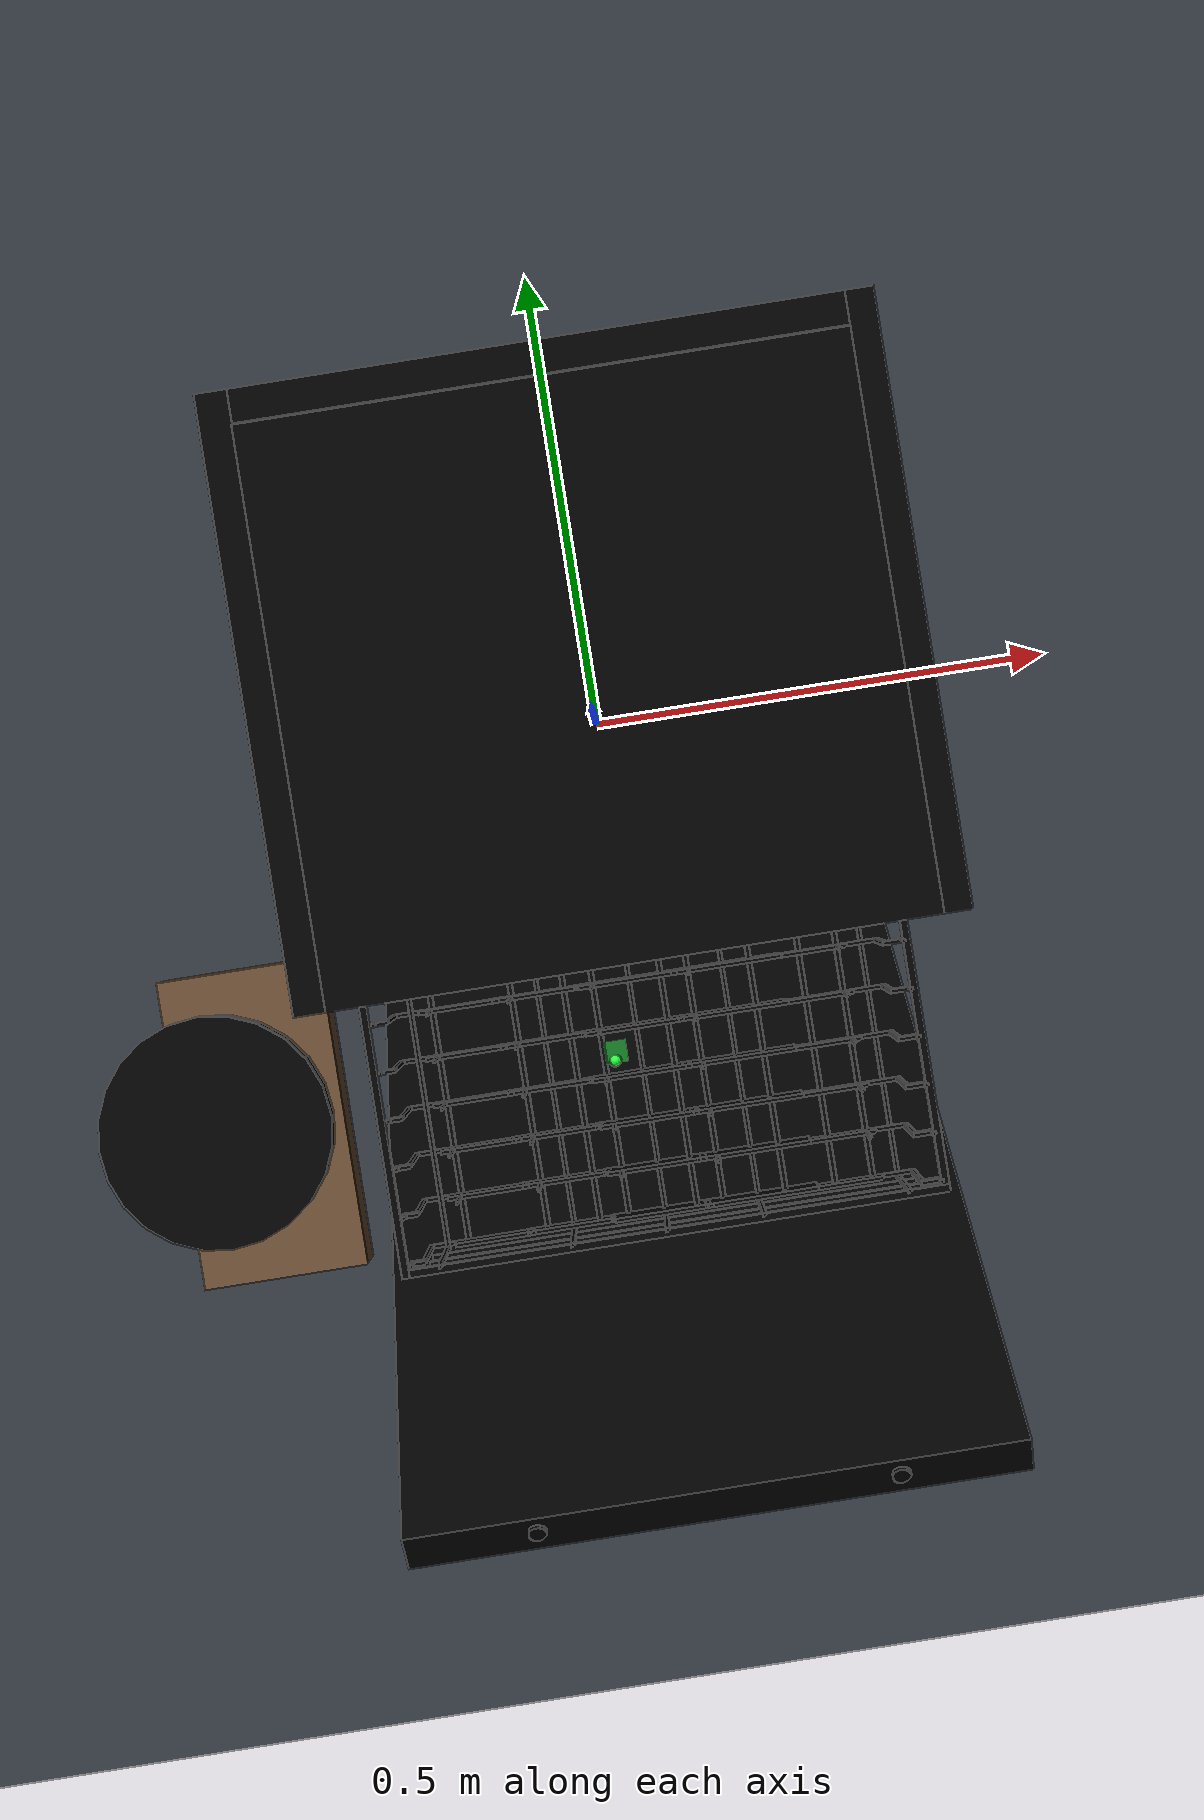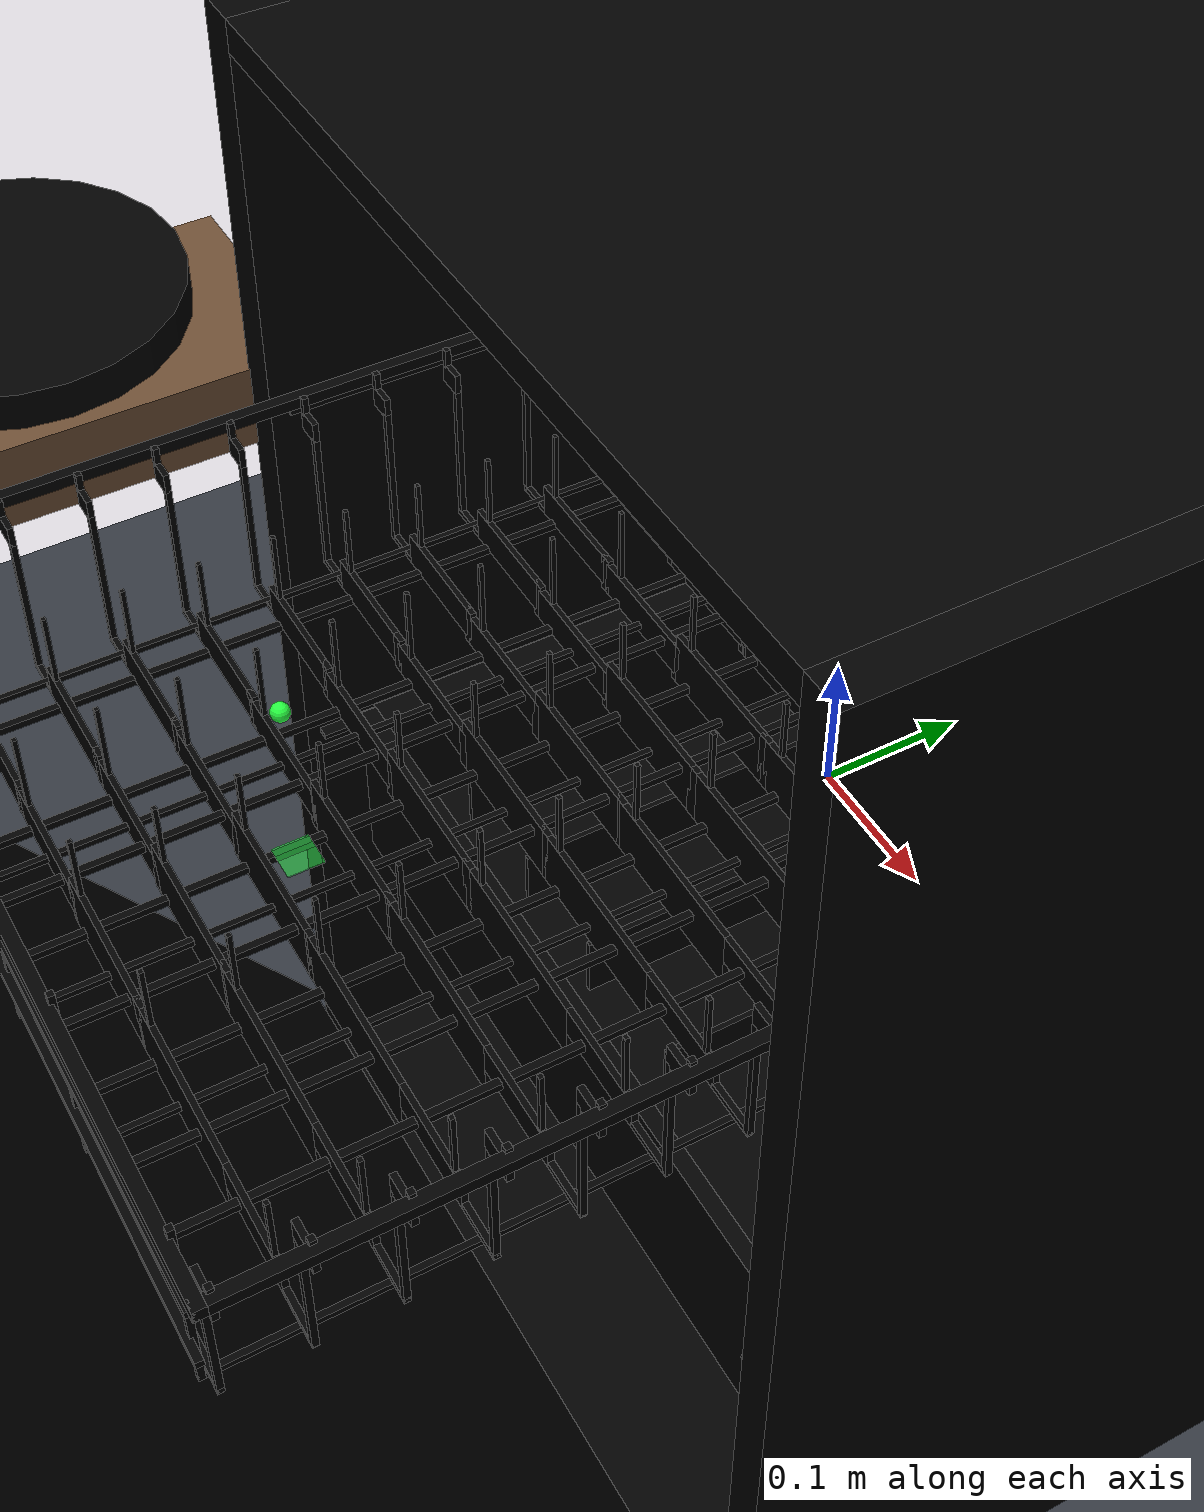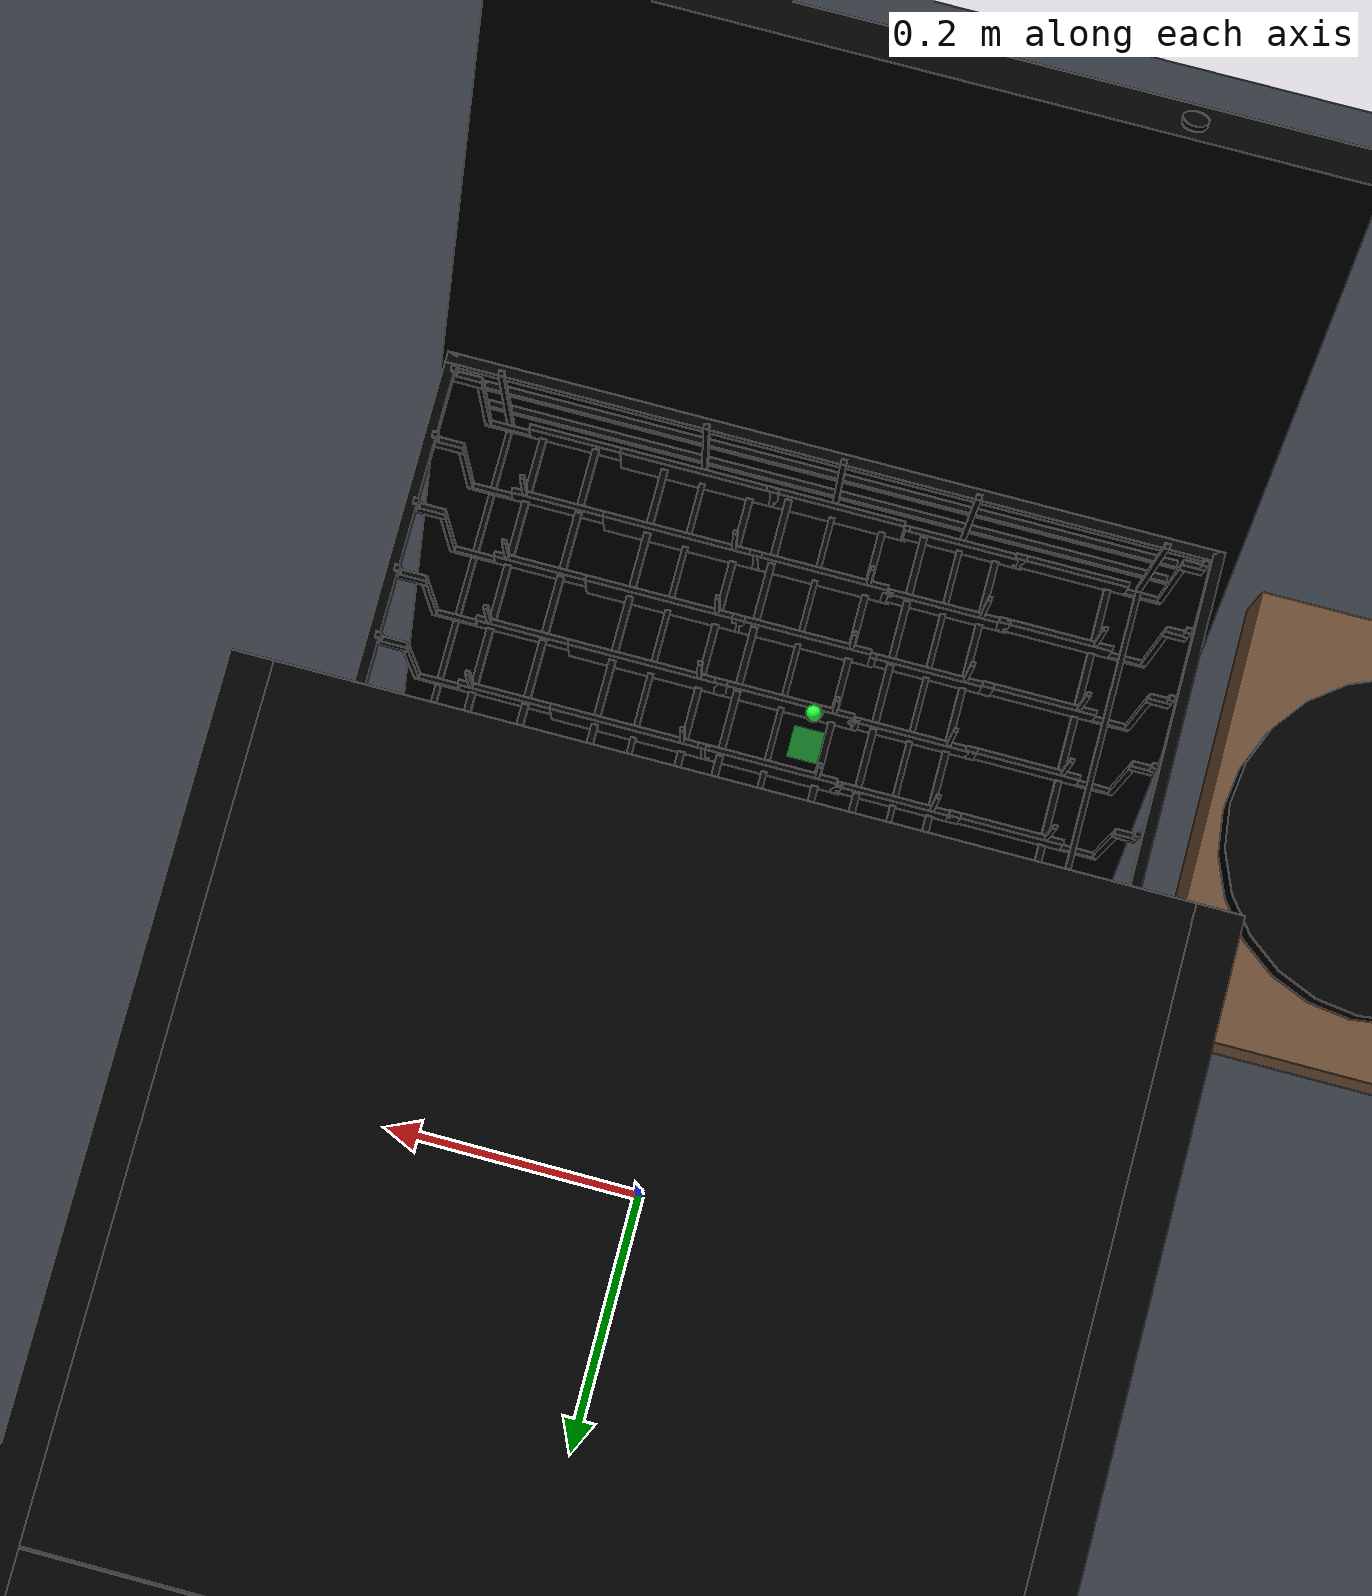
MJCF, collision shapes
<mujoco model="aao_dishwasher_plate">
  <compiler angle="radian" meshdir="../../../meshes" texturedir="../../../meshes"/>
  <option timestep="0.002" gravity="0 0 -9.81" integrator="implicitfast"/>
  <visual>
    <global azimuth="135" elevation="-20"/>
  </visual>
  <default>
    <joint damping="25" armature="0.02"/>
    <geom friction="1.0 0.02 0.002" solref="0.01 1"/>
    <position kp="600" kv="45"/>
  </default>

  <asset>
    <mesh name="plate2_mesh" file="dishwasher_plate/plate2/plate2.obj"/>
    <include file="includes/dishwasher031_assets.xml"/>
    <material name="floor" rgba="0.20 0.22 0.25 1"/>
    <material name="source_table" rgba="0.42 0.30 0.20 1"/>
    <material name="robot" rgba="0.25 0.55 0.85 1"/>
    <material name="target" rgba="0.15 0.75 0.25 0.65"/>
    <material name="plate" rgba="0.88 0.74 0.42 1"/>
  </asset>

  <worldbody>
    <light pos="0 -0.3 1.4" dir="0 0 -1" diffuse="0.9 0.9 0.9"/>
    <camera name="placement_camera" pos="0 -1.4 0.8"
            xyaxes="1 0 0 0 0.492 0.870" fovy="52"/>
    <geom name="floor" type="plane" pos="0 0 -0.478"
          size="1.0 1.2 0.05" material="floor"/>

    <body name="dishwasher">
      <include file="includes/dishwasher031_common.xml"/>

      <!-- The extracted upper rack uses mesh-derived local wire proxies. -->
      <body name="dishwasher_rack1" pos="0 -0.33 0">
        <include file="includes/dishwasher031_rack1_articulation.xml"/>
        <!-- Generated geometry and task contact policy are versioned separately. -->
        <include file="includes/dishwasher031_rack1_vertical_collision.xml"/>

        <body name="dishwasher_rack1_target" pos="-0.03487368 -0.0236405 0.20811805">
          <geom name="target_pad" type="box" pos="0 0 -0.120665074"
                size="0.012 0.012 0.0005" material="target"
                contype="0" conaffinity="0"/>
          <site name="dishwasher_rack1_target_site" pos="0 0 0"
                size="0.006" rgba="0.15 1 0.25 1"/>
        </body>
      </body>
    </body>

    <!-- Planner-only floor guard prevents trajectories below the appliance and rack. -->
    <geom name="planner_floor_guard" type="box" pos="0 -0.20 -0.035"
          size="0.75 0.90 0.025" rgba="0 0 0 0" contype="0" conaffinity="0"/>

    <geom name="source_table" type="box" pos="-0.405 -0.360 0.180560989"
          size="0.085 0.160 0.030" material="source_table"/>

    <!-- plate2 is horizontal: the mesh and collision-cylinder normal is +Z. -->
    <body name="plate2" pos="-0.450 -0.360 0.223671074">
      <freejoint name="plate2_joint"/>
      <site name="plate2_site" pos="0 0 0" size="0.006" rgba="1 0.75 0.2 1"/>
      <geom name="plate2_visual" type="mesh" mesh="plate2_mesh"
            pos="0.000074340 0.000103035 0.000636195"
            material="plate" mass="0" contype="0" conaffinity="0"/>
      <geom name="plate2_collision" type="cylinder" size="0.120165074 0.013110085"
            mass="0.35" rgba="0 0 0 0" condim="6" friction="1.0 0.1 0.02"/>
    </body>
  </worldbody>

  <actuator>
    <include file="includes/dishwasher031_actuators.xml"/>
  </actuator>
</mujoco>

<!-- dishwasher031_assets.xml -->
<mujocoinclude>
  <mesh name="dishwasher_body_visual"
        file="dishwasher_plate/dishwasher031/Body001.obj"/>
  <mesh name="dishwasher_door_visual"
        file="dishwasher_plate/dishwasher031/door.obj"/>
  <mesh name="dishwasher_button_lock_visual"
        file="dishwasher_plate/dishwasher031/button_lock.obj"/>
  <mesh name="dishwasher_button_power_visual"
        file="dishwasher_plate/dishwasher031/button_power.obj"/>
  <mesh name="dishwasher_rack0_visual"
        file="dishwasher_plate/dishwasher031/rack0.obj"/>
  <mesh name="dishwasher_rack1_visual"
        file="dishwasher_plate/dishwasher031/rack1.obj"/>
  <texture name="dishwasher_texture" type="2d"
           file="dishwasher_plate/dishwasher031/T_BC001.png"/>
  <material name="dishwasher" texture="dishwasher_texture"
            rgba="1 1 1 1" shininess="0.1" specular="0.6"/>
  <material name="rack" rgba="0.42 0.45 0.48 1"
            metallic="0.25" roughness="0.55"/>
</mujocoinclude>

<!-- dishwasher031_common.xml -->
<mujocoinclude>
  <geom name="dishwasher_body_visual_geom" type="mesh"
        mesh="dishwasher_body_visual" material="dishwasher"
        mass="0" contype="0" conaffinity="0"/>

  <body name="dishwasher_door"
        pos="0 -0.303386998368 0.087427061032"
        quat="0.954803187366 0.297238748139 0 0">
    <joint name="dishwasher_door_joint" type="hinge"
           axis="1 0 0"
           pos="-0.00171831 -0.29211199619594097 -0.4435629010736084"
           limited="true" range="0 0.6035987755982988"
           ref="0.6035987755982988" springref="0"
           damping="1" frictionloss="10" armature="1" stiffness="2"/>
    <geom name="dishwasher_door_visual_geom" type="mesh"
          mesh="dishwasher_door_visual" material="dishwasher"
          mass="0" contype="0" conaffinity="0"/>
    <geom name="dishwasher_door_main" type="box"
          pos="-0.00171831 -0.27046903 0.01473459"
          size="0.314526647329 0.021642966196 0.458297491074"
          rgba="0 0 0 0"/>
    <geom name="dishwasher_door_latch_right" type="box"
          pos="0.24632083 -0.31011658 0.39872193"
          size="0.012813650072 0.019381284714 0.016376437619"
          quat="0.730941057205 0 0.682440578938 0" rgba="0 0 0 0"/>
    <geom name="dishwasher_door_latch_left" type="box"
          pos="-0.23809594 -0.31011658 0.39885226"
          size="0.012395946309 0.019381269813 0.016752798110"
          quat="0.730941057205 0 0.682440578938 0" rgba="0 0 0 0"/>
    <geom name="dishwasher_door_handle" type="cylinder"
          pos="0.00388840 -0.33332097 0.39996758"
          size="0.012235971168 0.258230537176"
          quat="0.707106828690 0.000000012102 0.707106709480 -0.000000012102"
          rgba="0 0 0 0"/>

    <body name="dishwasher_button_lock">
      <joint name="dishwasher_button_lock_joint" type="slide"
             axis="0 0 -1" pos="-0.18298566 -0.26662981 0.47530904"
             limited="true" range="0 0.002" ref="0" springref="-0.0025"
             damping="1" frictionloss="1" armature="0.01" stiffness="4"/>
      <geom name="dishwasher_button_lock_visual_geom" type="mesh"
            mesh="dishwasher_button_lock_visual" material="dishwasher"
            mass="0" contype="0" conaffinity="0"/>
      <geom name="dishwasher_button_lock_collision" type="cylinder"
            pos="-0.18283316 -0.26663026 0.47586274"
            size="0.009277576581 0.002021603519"
            quat="0.707106709480 0 0 -0.707106828690" rgba="0 0 0 0"/>
    </body>
    <body name="dishwasher_button_power">
      <joint name="dishwasher_button_power_joint" type="slide"
             axis="0 0 -1" pos="0.18145567 -0.26662990 0.47530901"
             limited="true" range="0 0.002" ref="0" springref="-0.0025"
             damping="1" frictionloss="1" armature="0.01" stiffness="4"/>
      <geom name="dishwasher_button_power_visual_geom" type="mesh"
            mesh="dishwasher_button_power_visual" material="dishwasher"
            mass="0" contype="0" conaffinity="0"/>
      <geom name="dishwasher_button_power_collision" type="cylinder"
            pos="0.18147971 -0.26663026 0.47586274"
            size="0.009277576581 0.002021603519"
            quat="0.707106709480 0 0 -0.707106828690" rgba="0 0 0 0"/>
    </body>
  </body>

  <!-- Axis-aligned collision decomposition copied from the source cabinet. -->
  <geom name="dishwasher_cabinet_top" type="box"
        pos="0.00155940 0.03263054 0.46358112"
        size="0.293255686760 0.278490543365 0.010836720467" rgba="0 0 0 0"/>
  <geom name="dishwasher_cabinet_right" type="box"
        pos="0.30845612 0.04954802 0.00629329"
        size="0.013749126345 0.295408010483 0.468124508858" rgba="0 0 0 0"/>
  <geom name="dishwasher_cabinet_left" type="box"
        pos="-0.30654550 0.04954801 0.00629329"
        size="0.015659794211 0.295407950878 0.468124508858" rgba="0 0 0 0"/>
  <geom name="dishwasher_cabinet_back" type="box"
        pos="0.00155942 0.32865322 0.00629329"
        size="0.293255686760 0.016302794218 0.468124508858" rgba="0 0 0 0"/>
  <geom name="dishwasher_cabinet_bottom" type="box"
        pos="-0.00038596 0.04952301 -0.46985781"
        size="0.317077636719 0.295432984829 0.008026558906" rgba="0 0 0 0"/>
  <geom name="dishwasher_upper_rail_right" type="box"
        pos="0.28742397 0.04803570 0.19780329"
        size="0.007391098887 0.283953249454 0.001804872649" rgba="0 0 0 0"/>
  <geom name="dishwasher_upper_rail_left" type="box"
        pos="-0.28673527 0.04803570 0.19780329"
        size="0.004961001221 0.283953249454 0.001804872649" rgba="0 0 0 0"/>
  <geom name="dishwasher_lower_rail_left" type="box"
        pos="-0.28673527 0.04803570 -0.09955715"
        size="0.004961001221 0.283953249454 0.001804876374" rgba="0 0 0 0"/>
  <geom name="dishwasher_lower_rail_right" type="box"
        pos="0.28742397 0.04803570 -0.09955715"
        size="0.007391098887 0.283953249454 0.001804876374" rgba="0 0 0 0"/>

  <!-- The lower rack starts retracted and is entirely forbidden. -->
  <body name="dishwasher_rack0">
    <joint name="dishwasher_rack0_joint" type="slide"
           axis="0 -1 0" pos="-0.00163518 0.05106521 -0.15279360"
           limited="true" range="0 0.33" ref="0"
           damping="1" frictionloss="1" armature="0.01" stiffness="0.05"/>
    <geom name="dishwasher_rack0_visual_geom" type="mesh"
          mesh="dishwasher_rack0_visual" material="rack"
          mass="0" contype="0" conaffinity="0"/>
    <geom name="dishwasher_rack0_rib_0" type="box"
          pos="0.05465550 0.05172771 -0.15919490"
          size="0.001964055002 0.202991127968 0.026353538036" rgba="0 0 0 0"/>
    <geom name="dishwasher_rack0_rib_1" type="box"
          pos="-0.04838342 0.05172771 -0.15919490"
          size="0.001964055002 0.202991127968 0.026353538036" rgba="0 0 0 0"/>
    <geom name="dishwasher_rack0_rib_2" type="box"
          pos="-0.13689145 0.05172771 -0.15919490"
          size="0.001964055002 0.202991127968 0.026353538036" rgba="0 0 0 0"/>
    <geom name="dishwasher_rack0_rib_3" type="box"
          pos="-0.22374275 0.05172771 -0.15919490"
          size="0.001964055002 0.202991127968 0.026353538036" rgba="0 0 0 0"/>
    <geom name="dishwasher_rack0_base" type="box"
          pos="-0.00317875 0.05088568 -0.20264810"
          size="0.256795018911 0.250564277172 0.021035809070" rgba="0 0 0 0"/>
    <geom name="dishwasher_rack0_left" type="box"
          pos="-0.27093369 0.05203331 -0.14494359"
          size="0.010546132922 0.248831436038 0.059873435646" rgba="0 0 0 0"/>
    <geom name="dishwasher_rack0_right" type="box"
          pos="0.26400656 0.05203331 -0.14494359"
          size="0.010546132922 0.248831436038 0.059873435646" rgba="0 0 0 0"/>
    <geom name="dishwasher_rack0_front" type="box"
          pos="-0.00012753 -0.20295436 -0.15362094"
          size="0.277037441730 0.005895007402 0.070062935352" rgba="0 0 0 0"/>
    <geom name="dishwasher_rack0_rib_4" type="box"
          pos="0.21544147 0.05172771 -0.15919490"
          size="0.001964055002 0.202991127968 0.026353538036" rgba="0 0 0 0"/>
    <geom name="dishwasher_rack0_back" type="box"
          pos="-0.00012753 0.30668143 -0.15362094"
          size="0.277037441730 0.005895007402 0.070062935352" rgba="0 0 0 0"/>
  </body>
</mujocoinclude>

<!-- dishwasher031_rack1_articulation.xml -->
<mujocoinclude>
  <joint name="dishwasher_rack1_joint" type="slide"
         axis="0 -1 0" pos="-0.00163518 0.05106521 0.14311844"
         limited="true" range="0 0.33" ref="0.33"
         damping="1" frictionloss="1" armature="0.01" stiffness="0.05"/>
  <geom name="dishwasher_rack1_visual_geom" type="mesh"
        mesh="dishwasher_rack1_visual" material="rack"
        mass="0" contype="0" conaffinity="0"/>
</mujocoinclude>

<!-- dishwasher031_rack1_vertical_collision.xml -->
<mujocoinclude>
  <!-- Generated from proxy SHA-256 5222f3cba0f92a407f34aa2f312da616b84c59be2aa8076df999d4e5fc5a4350. -->
  <!-- Split policy SHA-256 03c2ceeb5299a301ae077681c6cb36bb31c12d472aaaee6d6d8dbd0db2ad434d. -->
  <geom name="dishwasher_rack1_wire_c000_s000_001" type="box" pos="-0.28412599999999999 0.051064999999999999 0.20480000000000001" size="0.0040000000000000036 0.26220900000000003 0.0040000000000000036" rgba="0 0 0 0"/>
  <geom name="dishwasher_rack1_wire_c000_s000_003" type="box" pos="-0.0016354999999999842 -0.20714399999999999 0.20480000000000001" size="0.28649049999999998 0.0040000000000000036 0.0040000000000000036" rgba="0 0 0 0"/>
  <geom name="dishwasher_rack1_wire_c000_s001_002" type="box" pos="-0.0016354999999999842 0.30927399999999999 0.20480000000000001" size="0.28649049999999998 0.0040000000000000036 0.0040000000000000036" rgba="0 0 0 0"/>
  <geom name="dishwasher_rack1_wire_c000_s002_003" type="box" pos="0.28085500000000002 0.051064999999999999 0.20480000000000001" size="0.0040000000000000036 0.26220900000000003 0.0040000000000000036" rgba="0 0 0 0"/>
  <geom name="dishwasher_rack1_wire_c001_s000_001" type="box" pos="-0.27631299999999998 -0.19936000000000001 0.2048065" size="0.0020000000000000018 0.0020000000000000018 0.0065915000000000001" rgba="0 0 0 0"/>
  <geom name="dishwasher_rack1_wire_c001_s001_002" type="box" pos="-0.26993599999999995 -0.19936000000000001 0.19273850000000001" size="0.0083769999999999956 0.0020000000000000018 0.0071454999999999991" rgba="0 0 0 0"/>
  <geom name="dishwasher_rack1_wire_c001_s002_003" type="box" pos="-0.2635595 -0.19936000000000001 0.1343115" size="0.0020005000000000162 0.0020000000000000018 0.052950500000000005" rgba="0 0 0 0"/>
  <geom name="dishwasher_rack1_wire_c001_s003_004" type="box" pos="-0.25096249999999998 -0.19936000000000001 0.083361000000000005" size="0.014597500000000013 0.0020000000000000018 0.0020000000000000018" rgba="0 0 0 0"/>
  <geom name="dishwasher_rack1_wire_c001_s004_005" type="box" pos="-0.19619999999999999 -0.19936000000000001 0.093303500000000011" size="0.040647000000000003 0.0020000000000000018 0.011942500000000002" rgba="0 0 0 0"/>
  <geom name="dishwasher_rack1_wire_c001_s005_006" type="box" pos="-0.15415100000000001 -0.19936000000000001 0.091241000000000003" size="0.0043279999999999985 0.0020000000000000018 0.014005000000000004" rgba="0 0 0 0"/>
  <geom name="dishwasher_rack1_wire_c001_s006_007" type="box" pos="-0.108962 -0.19936000000000001 0.089683499999999999" size="0.043794 0.0020000000000000018 0.0124475" rgba="0 0 0 0"/>
  <geom name="dishwasher_rack1_wire_c001_s007_008" type="box" pos="-0.064582000000000001 -0.19936000000000001 0.086962499999999998" size="0.0039150000000000018 0.0020000000000000018 0.015168500000000001" rgba="0 0 0 0"/>
  <geom name="dishwasher_rack1_wire_c001_s008_009" type="box" pos="-0.013715500000000002 -0.19936000000000001 0.091913499999999995" size="0.050121499999999999 0.0020000000000000018 0.020119499999999998" rgba="0 0 0 0"/>
  <geom name="dishwasher_rack1_wire_c001_s009_010" type="box" pos="0.037808499999999995 -0.19936000000000001 0.091778999999999999" size="0.0046105 0.0020000000000000018 0.020253999999999994" rgba="0 0 0 0"/>
  <geom name="dishwasher_rack1_wire_c001_s010_011" type="box" pos="0.097273999999999999 -0.19936000000000001 0.091659500000000005" size="0.058065000000000005 0.0020000000000000018 0.0201345" rgba="0 0 0 0"/>
  <geom name="dishwasher_rack1_wire_c001_s011_012" type="box" pos="0.190632 -0.19936000000000001 0.1013015" size="0.035306000000000004 0.0020000000000000018 0.010492500000000002" rgba="0 0 0 0"/>
  <geom name="dishwasher_rack1_wire_c001_s012_013" type="box" pos="0.24299100000000001 -0.19936000000000001 0.092809000000000003" size="0.01798000000000001 0.0020000000000000018 0.0020000000000000018" rgba="0 0 0 0"/>
  <geom name="dishwasher_rack1_wire_c001_s013_014" type="box" pos="0.25897100000000001 -0.19936000000000001 0.13914750000000001" size="0.0020000000000000018 0.0020000000000000018 0.048338500000000006" rgba="0 0 0 0"/>
  <geom name="dishwasher_rack1_wire_c001_s014_015" type="box" pos="0.26813200000000004 -0.19936000000000001 0.1926525" size="0.011161000000000004 0.0020000000000000018 0.0072844999999999993" rgba="0 0 0 0"/>
  <geom name="dishwasher_rack1_wire_c001_s015_016" type="box" pos="0.27729399999999998 -0.19936000000000001 0.20460800000000001" size="0.0020000000000000018 0.0020000000000000018 0.0067910000000000054" rgba="0 0 0 0"/>
  <geom name="dishwasher_rack1_wire_c002_s000_001" type="box" pos="-0.27631299999999998 -0.14915400000000001 0.2048065" size="0.0020000000000000018 0.0020000000000000018 0.0065915000000000001" rgba="0 0 0 0"/>
  <geom name="dishwasher_rack1_wire_c002_s001_002" type="box" pos="-0.26993599999999995 -0.14915400000000001 0.19273850000000001" size="0.0083769999999999956 0.0020000000000000018 0.0071454999999999991" rgba="0 0 0 0"/>
  <geom name="dishwasher_rack1_wire_c002_s002_003" type="box" pos="-0.2635595 -0.14915400000000001 0.1343115" size="0.0020005000000000162 0.0020000000000000018 0.052950500000000005" rgba="0 0 0 0"/>
  <geom name="dishwasher_rack1_wire_c002_s003_004" type="box" pos="-0.25096249999999998 -0.14915400000000001 0.083361000000000005" size="0.014597500000000013 0.0020000000000000018 0.0020000000000000018" rgba="0 0 0 0"/>
  <geom name="dishwasher_rack1_wire_c002_s004_005" type="box" pos="-0.19619999999999999 -0.14915400000000001 0.093303500000000011" size="0.040647000000000003 0.0020000000000000018 0.011942500000000002" rgba="0 0 0 0"/>
  <geom name="dishwasher_rack1_wire_c002_s005_006" type="box" pos="-0.15415100000000001 -0.14915400000000001 0.091241000000000003" size="0.0043279999999999985 0.0020000000000000018 0.014005000000000004" rgba="0 0 0 0"/>
  <geom name="dishwasher_rack1_wire_c002_s006_007" type="box" pos="-0.108962 -0.14915400000000001 0.089683499999999999" size="0.043794 0.0020000000000000018 0.0124475" rgba="0 0 0 0"/>
  <geom name="dishwasher_rack1_wire_c002_s007_008" type="box" pos="-0.064582000000000001 -0.14915400000000001 0.086962499999999998" size="0.0039150000000000018 0.0020000000000000018 0.015168500000000001" rgba="0 0 0 0"/>
  <geom name="dishwasher_rack1_wire_c002_s008_009" type="box" pos="-0.013715500000000002 -0.14915400000000001 0.091913499999999995" size="0.050121499999999999 0.0020000000000000018 0.020119499999999998" rgba="0 0 0 0"/>
  <geom name="dishwasher_rack1_wire_c002_s009_010" type="box" pos="0.037808499999999995 -0.14915400000000001 0.091778999999999999" size="0.0046105 0.0020000000000000018 0.020253999999999994" rgba="0 0 0 0"/>
  <geom name="dishwasher_rack1_wire_c002_s010_011" type="box" pos="0.097273999999999999 -0.14915400000000001 0.091659500000000005" size="0.058065000000000005 0.0020000000000000018 0.0201345" rgba="0 0 0 0"/>
  <geom name="dishwasher_rack1_wire_c002_s011_012" type="box" pos="0.190632 -0.14915400000000001 0.1013015" size="0.035306000000000004 0.0020000000000000018 0.010492500000000002" rgba="0 0 0 0"/>
  <geom name="dishwasher_rack1_wire_c002_s012_013" type="box" pos="0.24299100000000001 -0.14915400000000001 0.092809000000000003" size="0.01798000000000001 0.0020000000000000018 0.0020000000000000018" rgba="0 0 0 0"/>
  <geom name="dishwasher_rack1_wire_c002_s013_014" type="box" pos="0.25897100000000001 -0.14915400000000001 0.13914750000000001" size="0.0020000000000000018 0.0020000000000000018 0.048338500000000006" rgba="0 0 0 0"/>
  <geom name="dishwasher_rack1_wire_c002_s014_015" type="box" pos="0.26813200000000004 -0.14915400000000001 0.1926525" size="0.011161000000000004 0.0020000000000000018 0.0072844999999999993" rgba="0 0 0 0"/>
  <geom name="dishwasher_rack1_wire_c002_s015_016" type="box" pos="0.27729399999999998 -0.14915400000000001 0.20460800000000001" size="0.0020000000000000018 0.0020000000000000018 0.0067910000000000054" rgba="0 0 0 0"/>
  <geom name="dishwasher_rack1_wire_c003_s000_001" type="box" pos="-0.27631299999999998 -0.098948999999999995 0.2048065" size="0.0020000000000000018 0.0020000000000000018 0.0065915000000000001" rgba="0 0 0 0"/>
  <geom name="dishwasher_rack1_wire_c003_s001_002" type="box" pos="-0.26993599999999995 -0.098948999999999995 0.19273850000000001" size="0.0083769999999999956 0.0020000000000000018 0.0071454999999999991" rgba="0 0 0 0"/>
  <geom name="dishwasher_rack1_wire_c003_s002_003" type="box" pos="-0.2635595 -0.098948999999999995 0.1343115" size="0.0020005000000000162 0.0020000000000000018 0.052950500000000005" rgba="0 0 0 0"/>
  <geom name="dishwasher_rack1_wire_c003_s003_004" type="box" pos="-0.25096249999999998 -0.098948999999999995 0.083361000000000005" size="0.014597500000000013 0.0020000000000000018 0.0020000000000000018" rgba="0 0 0 0"/>
  <geom name="dishwasher_rack1_wire_c003_s004_005" type="box" pos="-0.19619999999999999 -0.098948999999999995 0.093303500000000011" size="0.040647000000000003 0.0020000000000000018 0.011942500000000002" rgba="0 0 0 0"/>
  <geom name="dishwasher_rack1_wire_c003_s005_006" type="box" pos="-0.15415100000000001 -0.098948999999999995 0.091241000000000003" size="0.0043279999999999985 0.0020000000000000018 0.014005000000000004" rgba="0 0 0 0"/>
  <geom name="dishwasher_rack1_wire_c003_s006_007" type="box" pos="-0.108962 -0.098948999999999995 0.089683499999999999" size="0.043794 0.0020000000000000018 0.0124475" rgba="0 0 0 0"/>
  <geom name="dishwasher_rack1_wire_c003_s007_008" type="box" pos="-0.064582000000000001 -0.098948999999999995 0.086962499999999998" size="0.0039150000000000018 0.0020000000000000018 0.015168500000000001" rgba="0 0 0 0"/>
  <geom name="dishwasher_rack1_wire_c003_s008_009" type="box" pos="-0.013715500000000002 -0.098948999999999995 0.091913499999999995" size="0.050121499999999999 0.0020000000000000018 0.020119499999999998" rgba="0 0 0 0"/>
  <geom name="dishwasher_rack1_wire_c003_s009_010" type="box" pos="0.037808499999999995 -0.098948999999999995 0.091778999999999999" size="0.0046105 0.0020000000000000018 0.020253999999999994" rgba="0 0 0 0"/>
  <geom name="dishwasher_rack1_wire_c003_s010_011" type="box" pos="0.097273999999999999 -0.098948999999999995 0.091659500000000005" size="0.058065000000000005 0.0020000000000000018 0.0201345" rgba="0 0 0 0"/>
  <geom name="dishwasher_rack1_wire_c003_s011_012" type="box" pos="0.190632 -0.098948999999999995 0.1013015" size="0.035306000000000004 0.0020000000000000018 0.010492500000000002" rgba="0 0 0 0"/>
  <geom name="dishwasher_rack1_wire_c003_s012_013" type="box" pos="0.24299100000000001 -0.098948999999999995 0.092809000000000003" size="0.01798000000000001 0.0020000000000000018 0.0020000000000000018" rgba="0 0 0 0"/>
  <geom name="dishwasher_rack1_wire_c003_s013_014" type="box" pos="0.25897100000000001 -0.098948999999999995 0.13914750000000001" size="0.0020000000000000018 0.0020000000000000018 0.048338500000000006" rgba="0 0 0 0"/>
  <geom name="dishwasher_rack1_wire_c003_s014_015" type="box" pos="0.26813200000000004 -0.098948999999999995 0.1926525" size="0.011161000000000004 0.0020000000000000018 0.0072844999999999993" rgba="0 0 0 0"/>
  <geom name="dishwasher_rack1_wire_c003_s015_016" type="box" pos="0.27729399999999998 -0.098948999999999995 0.20460800000000001" size="0.0020000000000000018 0.0020000000000000018 0.0067910000000000054" rgba="0 0 0 0"/>
  <geom name="dishwasher_rack1_wire_c004_s000_001" type="box" pos="-0.27631299999999998 -0.048743000000000002 0.2048065" size="0.0020000000000000018 0.0020000000000000018 0.0065915000000000001" rgba="0 0 0 0"/>
  <geom name="dishwasher_rack1_wire_c004_s001_002" type="box" pos="-0.26993599999999995 -0.048743000000000002 0.19273850000000001" size="0.0083769999999999956 0.0020000000000000018 0.0071454999999999991" rgba="0 0 0 0"/>
  <geom name="dishwasher_rack1_wire_c004_s002_003" type="box" pos="-0.2635595 -0.048743000000000002 0.1343115" size="0.0020005000000000162 0.0020000000000000018 0.052950500000000005" rgba="0 0 0 0"/>
  <geom name="dishwasher_rack1_wire_c004_s003_004" type="box" pos="-0.25096249999999998 -0.048743000000000002 0.083361000000000005" size="0.014597500000000013 0.0020000000000000018 0.0020000000000000018" rgba="0 0 0 0"/>
  <geom name="dishwasher_rack1_wire_c004_s004_005" type="box" pos="-0.19619999999999999 -0.048743000000000002 0.093303500000000011" size="0.040647000000000003 0.0020000000000000018 0.011942500000000002" rgba="0 0 0 0"/>
  <geom name="dishwasher_rack1_wire_c004_s005_006" type="box" pos="-0.15415100000000001 -0.048743000000000002 0.091241000000000003" size="0.0043279999999999985 0.0020000000000000018 0.014005000000000004" rgba="0 0 0 0"/>
  <geom name="dishwasher_rack1_wire_c004_s006_007" type="box" pos="-0.108962 -0.048743000000000002 0.089683499999999999" size="0.043794 0.0020000000000000018 0.0124475" rgba="0 0 0 0"/>
  <geom name="dishwasher_rack1_wire_c004_s007_008" type="box" pos="-0.064582000000000001 -0.048743000000000002 0.086962499999999998" size="0.0039150000000000018 0.0020000000000000018 0.015168500000000001" rgba="0 0 0 0"/>
  <geom name="dishwasher_rack1_wire_c004_s008_009" type="box" pos="-0.013715500000000002 -0.048743000000000002 0.091913499999999995" size="0.050121499999999999 0.0020000000000000018 0.020119499999999998" rgba="0 0 0 0"/>
  <geom name="dishwasher_rack1_wire_c004_s009_010" type="box" pos="0.037808499999999995 -0.048743000000000002 0.091778999999999999" size="0.0046105 0.0020000000000000018 0.020253999999999994" rgba="0 0 0 0"/>
  <geom name="dishwasher_rack1_wire_c004_s010_011" type="box" pos="0.097273999999999999 -0.048743000000000002 0.091659500000000005" size="0.058065000000000005 0.0020000000000000018 0.0201345" rgba="0 0 0 0"/>
  <geom name="dishwasher_rack1_wire_c004_s011_012" type="box" pos="0.190632 -0.048743000000000002 0.1013015" size="0.035306000000000004 0.0020000000000000018 0.010492500000000002" rgba="0 0 0 0"/>
  <geom name="dishwasher_rack1_wire_c004_s012_013" type="box" pos="0.24299100000000001 -0.048743000000000002 0.092809000000000003" size="0.01798000000000001 0.0020000000000000018 0.0020000000000000018" rgba="0 0 0 0"/>
  <geom name="dishwasher_rack1_wire_c004_s013_014" type="box" pos="0.25897100000000001 -0.048743000000000002 0.13914750000000001" size="0.0020000000000000018 0.0020000000000000018 0.048338500000000006" rgba="0 0 0 0"/>
  <geom name="dishwasher_rack1_wire_c004_s014_015" type="box" pos="0.26813200000000004 -0.048743000000000002 0.1926525" size="0.011161000000000004 0.0020000000000000018 0.0072844999999999993" rgba="0 0 0 0"/>
  <geom name="dishwasher_rack1_wire_c004_s015_016" type="box" pos="0.27729399999999998 -0.048743000000000002 0.20460800000000001" size="0.0020000000000000018 0.0020000000000000018 0.0067910000000000054" rgba="0 0 0 0"/>
  <geom name="dishwasher_rack1_wire_c005_s000_001" type="box" pos="-0.27631299999999998 0.001462 0.2048065" size="0.0020000000000000018 0.002 0.0065915000000000001" rgba="0 0 0 0"/>
  <geom name="dishwasher_rack1_wire_c005_s001_002" type="box" pos="-0.26993599999999995 0.001462 0.19273850000000001" size="0.0083769999999999956 0.002 0.0071454999999999991" rgba="0 0 0 0"/>
  <geom name="dishwasher_rack1_wire_c005_s002_003" type="box" pos="-0.2635595 0.001462 0.1343115" size="0.0020005000000000162 0.002 0.052950500000000005" rgba="0 0 0 0"/>
  <geom name="dishwasher_rack1_wire_c005_s003_004" type="box" pos="-0.25096249999999998 0.001462 0.083361000000000005" size="0.014597500000000013 0.002 0.0020000000000000018" rgba="0 0 0 0"/>
  <geom name="dishwasher_rack1_wire_c005_s004_005" type="box" pos="-0.19619999999999999 0.001462 0.093303500000000011" size="0.040647000000000003 0.002 0.011942500000000002" rgba="0 0 0 0"/>
  <geom name="dishwasher_rack1_wire_c005_s005_006" type="box" pos="-0.15415100000000001 0.001462 0.091241000000000003" size="0.0043279999999999985 0.002 0.014005000000000004" rgba="0 0 0 0"/>
  <geom name="dishwasher_rack1_wire_c005_s006_007" type="box" pos="-0.108962 0.001462 0.089683499999999999" size="0.043794 0.002 0.0124475" rgba="0 0 0 0"/>
  <geom name="dishwasher_rack1_wire_c005_s007_008" type="box" pos="-0.064582000000000001 0.001462 0.086962499999999998" size="0.0039150000000000018 0.002 0.015168500000000001" rgba="0 0 0 0"/>
  <geom name="dishwasher_rack1_wire_c005_s008_009" type="box" pos="-0.013715500000000002 0.001462 0.091913499999999995" size="0.050121499999999999 0.002 0.020119499999999998" rgba="0 0 0 0"/>
  <geom name="dishwasher_rack1_wire_c005_s009_010" type="box" pos="0.037808499999999995 0.001462 0.091778999999999999" size="0.0046105 0.002 0.020253999999999994" rgba="0 0 0 0"/>
  <geom name="dishwasher_rack1_wire_c005_s010_011" type="box" pos="0.097273999999999999 0.001462 0.091659500000000005" size="0.058065000000000005 0.002 0.0201345" rgba="0 0 0 0"/>
  <geom name="dishwasher_rack1_wire_c005_s011_012" type="box" pos="0.190632 0.001462 0.1013015" size="0.035306000000000004 0.002 0.010492500000000002" rgba="0 0 0 0"/>
  <geom name="dishwasher_rack1_wire_c005_s012_013" type="box" pos="0.24299100000000001 0.001462 0.092809000000000003" size="0.01798000000000001 0.002 0.0020000000000000018" rgba="0 0 0 0"/>
  <geom name="dishwasher_rack1_wire_c005_s013_014" type="box" pos="0.25897100000000001 0.001462 0.13914750000000001" size="0.0020000000000000018 0.002 0.048338500000000006" rgba="0 0 0 0"/>
  <geom name="dishwasher_rack1_wire_c005_s014_015" type="box" pos="0.26813200000000004 0.001462 0.1926525" size="0.011161000000000004 0.002 0.0072844999999999993" rgba="0 0 0 0"/>
  <geom name="dishwasher_rack1_wire_c005_s015_016" type="box" pos="0.27729399999999998 0.001462 0.20460800000000001" size="0.0020000000000000018 0.002 0.0067910000000000054" rgba="0 0 0 0"/>
  <geom name="dishwasher_rack1_wire_c006_s000_001" type="box" pos="-0.27631299999999998 0.051667000000000005 0.2048065" size="0.0020000000000000018 0.0019999999999999983 0.0065915000000000001" rgba="0 0 0 0"/>
  <geom name="dishwasher_rack1_wire_c006_s001_002" type="box" pos="-0.26993599999999995 0.051667000000000005 0.19273850000000001" size="0.0083769999999999956 0.0019999999999999983 0.0071454999999999991" rgba="0 0 0 0"/>
  <geom name="dishwasher_rack1_wire_c006_s002_003" type="box" pos="-0.2635595 0.051667000000000005 0.1343115" size="0.0020005000000000162 0.0019999999999999983 0.052950500000000005" rgba="0 0 0 0"/>
  <geom name="dishwasher_rack1_wire_c006_s003_004" type="box" pos="-0.25096249999999998 0.051667000000000005 0.083361000000000005" size="0.014597500000000013 0.0019999999999999983 0.0020000000000000018" rgba="0 0 0 0"/>
  <geom name="dishwasher_rack1_wire_c006_s004_005" type="box" pos="-0.19619999999999999 0.051667000000000005 0.093303500000000011" size="0.040647000000000003 0.0019999999999999983 0.011942500000000002" rgba="0 0 0 0"/>
  <geom name="dishwasher_rack1_wire_c006_s005_006" type="box" pos="-0.15415100000000001 0.051667000000000005 0.091241000000000003" size="0.0043279999999999985 0.0019999999999999983 0.014005000000000004" rgba="0 0 0 0"/>
  <geom name="dishwasher_rack1_wire_c006_s006_007" type="box" pos="-0.108962 0.051667000000000005 0.089683499999999999" size="0.043794 0.0019999999999999983 0.0124475" rgba="0 0 0 0"/>
  <geom name="dishwasher_rack1_wire_c006_s007_008" type="box" pos="-0.064582000000000001 0.051667000000000005 0.086962499999999998" size="0.0039150000000000018 0.0019999999999999983 0.015168500000000001" rgba="0 0 0 0"/>
  <geom name="dishwasher_rack1_wire_c006_s008_009" type="box" pos="-0.013715500000000002 0.051667000000000005 0.091913499999999995" size="0.050121499999999999 0.0019999999999999983 0.020119499999999998" rgba="0 0 0 0"/>
  <geom name="dishwasher_rack1_wire_c006_s009_010" type="box" pos="0.037808499999999995 0.051667000000000005 0.091778999999999999" size="0.0046105 0.0019999999999999983 0.020253999999999994" rgba="0 0 0 0"/>
  <geom name="dishwasher_rack1_wire_c006_s010_011" type="box" pos="0.097273999999999999 0.051667000000000005 0.091659500000000005" size="0.058065000000000005 0.0019999999999999983 0.0201345" rgba="0 0 0 0"/>
  <geom name="dishwasher_rack1_wire_c006_s011_012" type="box" pos="0.190632 0.051667000000000005 0.1013015" size="0.035306000000000004 0.0019999999999999983 0.010492500000000002" rgba="0 0 0 0"/>
  <geom name="dishwasher_rack1_wire_c006_s012_013" type="box" pos="0.24299100000000001 0.051667000000000005 0.092809000000000003" size="0.01798000000000001 0.0019999999999999983 0.0020000000000000018" rgba="0 0 0 0"/>
  <geom name="dishwasher_rack1_wire_c006_s013_014" type="box" pos="0.25897100000000001 0.051667000000000005 0.13914750000000001" size="0.0020000000000000018 0.0019999999999999983 0.048338500000000006" rgba="0 0 0 0"/>
  <geom name="dishwasher_rack1_wire_c006_s014_015" type="box" pos="0.26813200000000004 0.051667000000000005 0.1926525" size="0.011161000000000004 0.0019999999999999983 0.0072844999999999993" rgba="0 0 0 0"/>
  <geom name="dishwasher_rack1_wire_c006_s015_016" type="box" pos="0.27729399999999998 0.051667000000000005 0.20460800000000001" size="0.0020000000000000018 0.0019999999999999983 0.0067910000000000054" rgba="0 0 0 0"/>
  <geom name="dishwasher_rack1_wire_c007_s000_001" type="box" pos="-0.27631299999999998 0.10187299999999999 0.2048065" size="0.0020000000000000018 0.0019999999999999948 0.0065915000000000001" rgba="0 0 0 0"/>
  <geom name="dishwasher_rack1_wire_c007_s001_002" type="box" pos="-0.26993599999999995 0.10187299999999999 0.19273850000000001" size="0.0083769999999999956 0.0019999999999999948 0.0071454999999999991" rgba="0 0 0 0"/>
  <geom name="dishwasher_rack1_wire_c007_s002_003" type="box" pos="-0.2635595 0.10187299999999999 0.1343115" size="0.0020005000000000162 0.0019999999999999948 0.052950500000000005" rgba="0 0 0 0"/>
  <geom name="dishwasher_rack1_wire_c007_s003_004" type="box" pos="-0.25096249999999998 0.10187299999999999 0.083361000000000005" size="0.014597500000000013 0.0019999999999999948 0.0020000000000000018" rgba="0 0 0 0"/>
  <geom name="dishwasher_rack1_wire_c007_s004_005" type="box" pos="-0.19619999999999999 0.10187299999999999 0.093303500000000011" size="0.040647000000000003 0.0019999999999999948 0.011942500000000002" rgba="0 0 0 0"/>
  <geom name="dishwasher_rack1_wire_c007_s005_006" type="box" pos="-0.15415100000000001 0.10187299999999999 0.091241000000000003" size="0.0043279999999999985 0.0019999999999999948 0.014005000000000004" rgba="0 0 0 0"/>
  <geom name="dishwasher_rack1_wire_c007_s006_007" type="box" pos="-0.108962 0.10187299999999999 0.089683499999999999" size="0.043794 0.0019999999999999948 0.0124475" rgba="0 0 0 0"/>
  <geom name="dishwasher_rack1_wire_c007_s007_008" type="box" pos="-0.064582000000000001 0.10187299999999999 0.086962499999999998" size="0.0039150000000000018 0.0019999999999999948 0.015168500000000001" rgba="0 0 0 0"/>
  <geom name="dishwasher_rack1_wire_c007_s008_009" type="box" pos="-0.013715500000000002 0.10187299999999999 0.091913499999999995" size="0.050121499999999999 0.0019999999999999948 0.020119499999999998" rgba="0 0 0 0"/>
  <geom name="dishwasher_rack1_wire_c007_s009_010" type="box" pos="0.037808499999999995 0.10187299999999999 0.091778999999999999" size="0.0046105 0.0019999999999999948 0.020253999999999994" rgba="0 0 0 0"/>
  <geom name="dishwasher_rack1_wire_c007_s010_011" type="box" pos="0.097273999999999999 0.10187299999999999 0.091659500000000005" size="0.058065000000000005 0.0019999999999999948 0.0201345" rgba="0 0 0 0"/>
  <geom name="dishwasher_rack1_wire_c007_s011_012" type="box" pos="0.190632 0.10187299999999999 0.1013015" size="0.035306000000000004 0.0019999999999999948 0.010492500000000002" rgba="0 0 0 0"/>
  <geom name="dishwasher_rack1_wire_c007_s012_013" type="box" pos="0.24299100000000001 0.10187299999999999 0.092809000000000003" size="0.01798000000000001 0.0019999999999999948 0.0020000000000000018" rgba="0 0 0 0"/>
  <geom name="dishwasher_rack1_wire_c007_s013_014" type="box" pos="0.25897100000000001 0.10187299999999999 0.13914750000000001" size="0.0020000000000000018 0.0019999999999999948 0.048338500000000006" rgba="0 0 0 0"/>
  <geom name="dishwasher_rack1_wire_c007_s014_015" type="box" pos="0.26813200000000004 0.10187299999999999 0.1926525" size="0.011161000000000004 0.0019999999999999948 0.0072844999999999993" rgba="0 0 0 0"/>
  <geom name="dishwasher_rack1_wire_c007_s015_016" type="box" pos="0.27729399999999998 0.10187299999999999 0.20460800000000001" size="0.0020000000000000018 0.0019999999999999948 0.0067910000000000054" rgba="0 0 0 0"/>
  <geom name="dishwasher_rack1_wire_c008_s000_001" type="box" pos="-0.27631299999999998 0.15207799999999999 0.2048065" size="0.0020000000000000018 0.0020000000000000018 0.0065915000000000001" rgba="0 0 0 0"/>
  <geom name="dishwasher_rack1_wire_c008_s001_002" type="box" pos="-0.26993599999999995 0.15207799999999999 0.19273850000000001" size="0.0083769999999999956 0.0020000000000000018 0.0071454999999999991" rgba="0 0 0 0"/>
  <geom name="dishwasher_rack1_wire_c008_s002_003" type="box" pos="-0.2635595 0.15207799999999999 0.1343115" size="0.0020005000000000162 0.0020000000000000018 0.052950500000000005" rgba="0 0 0 0"/>
  <geom name="dishwasher_rack1_wire_c008_s003_004" type="box" pos="-0.25096249999999998 0.15207799999999999 0.083361000000000005" size="0.014597500000000013 0.0020000000000000018 0.0020000000000000018" rgba="0 0 0 0"/>
  <geom name="dishwasher_rack1_wire_c008_s004_005" type="box" pos="-0.19619999999999999 0.15207799999999999 0.093303500000000011" size="0.040647000000000003 0.0020000000000000018 0.011942500000000002" rgba="0 0 0 0"/>
  <geom name="dishwasher_rack1_wire_c008_s005_006" type="box" pos="-0.15415100000000001 0.15207799999999999 0.091241000000000003" size="0.0043279999999999985 0.0020000000000000018 0.014005000000000004" rgba="0 0 0 0"/>
  <geom name="dishwasher_rack1_wire_c008_s006_007" type="box" pos="-0.108962 0.15207799999999999 0.089683499999999999" size="0.043794 0.0020000000000000018 0.0124475" rgba="0 0 0 0"/>
  <geom name="dishwasher_rack1_wire_c008_s007_008" type="box" pos="-0.064582000000000001 0.15207799999999999 0.086962499999999998" size="0.0039150000000000018 0.0020000000000000018 0.015168500000000001" rgba="0 0 0 0"/>
  <geom name="dishwasher_rack1_wire_c008_s008_009" type="box" pos="-0.013715500000000002 0.15207799999999999 0.091913499999999995" size="0.050121499999999999 0.0020000000000000018 0.020119499999999998" rgba="0 0 0 0"/>
  <geom name="dishwasher_rack1_wire_c008_s009_010" type="box" pos="0.037808499999999995 0.15207799999999999 0.091778999999999999" size="0.0046105 0.0020000000000000018 0.020253999999999994" rgba="0 0 0 0"/>
  <geom name="dishwasher_rack1_wire_c008_s010_011" type="box" pos="0.097273999999999999 0.15207799999999999 0.091659500000000005" size="0.058065000000000005 0.0020000000000000018 0.0201345" rgba="0 0 0 0"/>
  <geom name="dishwasher_rack1_wire_c008_s011_012" type="box" pos="0.190632 0.15207799999999999 0.1013015" size="0.035306000000000004 0.0020000000000000018 0.010492500000000002" rgba="0 0 0 0"/>
  <geom name="dishwasher_rack1_wire_c008_s012_013" type="box" pos="0.24299100000000001 0.15207799999999999 0.092809000000000003" size="0.01798000000000001 0.0020000000000000018 0.0020000000000000018" rgba="0 0 0 0"/>
  <geom name="dishwasher_rack1_wire_c008_s013_014" type="box" pos="0.25897100000000001 0.15207799999999999 0.13914750000000001" size="0.0020000000000000018 0.0020000000000000018 0.048338500000000006" rgba="0 0 0 0"/>
  <geom name="dishwasher_rack1_wire_c008_s014_015" type="box" pos="0.26813200000000004 0.15207799999999999 0.1926525" size="0.011161000000000004 0.0020000000000000018 0.0072844999999999993" rgba="0 0 0 0"/>
  <geom name="dishwasher_rack1_wire_c008_s015_016" type="box" pos="0.27729399999999998 0.15207799999999999 0.20460800000000001" size="0.0020000000000000018 0.0020000000000000018 0.0067910000000000054" rgba="0 0 0 0"/>
  <geom name="dishwasher_rack1_wire_c009_s000_001" type="box" pos="-0.27631299999999998 0.2022835 0.2048065" size="0.0020000000000000018 0.0019995000000000013 0.0065915000000000001" rgba="0 0 0 0"/>
  <geom name="dishwasher_rack1_wire_c009_s001_002" type="box" pos="-0.26993599999999995 0.2022835 0.19273850000000001" size="0.0083769999999999956 0.0019995000000000013 0.0071454999999999991" rgba="0 0 0 0"/>
  <geom name="dishwasher_rack1_wire_c009_s002_003" type="box" pos="-0.2635595 0.2022835 0.1343115" size="0.0020005000000000162 0.0019995000000000013 0.052950500000000005" rgba="0 0 0 0"/>
  <geom name="dishwasher_rack1_wire_c009_s003_004" type="box" pos="-0.25096249999999998 0.2022835 0.083361000000000005" size="0.014597500000000013 0.0019995000000000013 0.0020000000000000018" rgba="0 0 0 0"/>
  <geom name="dishwasher_rack1_wire_c009_s004_005" type="box" pos="-0.19619999999999999 0.2022835 0.093303500000000011" size="0.040647000000000003 0.0019995000000000013 0.011942500000000002" rgba="0 0 0 0"/>
  <geom name="dishwasher_rack1_wire_c009_s005_006" type="box" pos="-0.15415100000000001 0.2022835 0.091241000000000003" size="0.0043279999999999985 0.0019995000000000013 0.014005000000000004" rgba="0 0 0 0"/>
  <geom name="dishwasher_rack1_wire_c009_s006_007" type="box" pos="-0.108962 0.2022835 0.089683499999999999" size="0.043794 0.0019995000000000013 0.0124475" rgba="0 0 0 0"/>
  <geom name="dishwasher_rack1_wire_c009_s007_008" type="box" pos="-0.064582000000000001 0.2022835 0.086962499999999998" size="0.0039150000000000018 0.0019995000000000013 0.015168500000000001" rgba="0 0 0 0"/>
  <geom name="dishwasher_rack1_wire_c009_s008_009" type="box" pos="-0.013715500000000002 0.2022835 0.091913499999999995" size="0.050121499999999999 0.0019995000000000013 0.020119499999999998" rgba="0 0 0 0"/>
  <geom name="dishwasher_rack1_wire_c009_s009_010" type="box" pos="0.037808499999999995 0.2022835 0.091778999999999999" size="0.0046105 0.0019995000000000013 0.020253999999999994" rgba="0 0 0 0"/>
  <geom name="dishwasher_rack1_wire_c009_s010_011" type="box" pos="0.097273999999999999 0.2022835 0.091659500000000005" size="0.058065000000000005 0.0019995000000000013 0.0201345" rgba="0 0 0 0"/>
  <geom name="dishwasher_rack1_wire_c009_s011_012" type="box" pos="0.190632 0.2022835 0.1013015" size="0.035306000000000004 0.0019995000000000013 0.010492500000000002" rgba="0 0 0 0"/>
  <geom name="dishwasher_rack1_wire_c009_s012_013" type="box" pos="0.24299100000000001 0.2022835 0.092809000000000003" size="0.01798000000000001 0.0019995000000000013 0.0020000000000000018" rgba="0 0 0 0"/>
  <geom name="dishwasher_rack1_wire_c009_s013_014" type="box" pos="0.25897100000000001 0.2022835 0.13914750000000001" size="0.0020000000000000018 0.0019995000000000013 0.048338500000000006" rgba="0 0 0 0"/>
  <geom name="dishwasher_rack1_wire_c009_s014_015" type="box" pos="0.26813200000000004 0.2022835 0.1926525" size="0.011161000000000004 0.0019995000000000013 0.0072844999999999993" rgba="0 0 0 0"/>
  <geom name="dishwasher_rack1_wire_c009_s015_016" type="box" pos="0.27729399999999998 0.2022835 0.20460800000000001" size="0.0020000000000000018 0.0019995000000000013 0.0067910000000000054" rgba="0 0 0 0"/>
  <geom name="dishwasher_rack1_wire_c010_s000_001" type="box" pos="-0.27631299999999998 0.25248900000000002 0.2048065" size="0.0020000000000000018 0.0020000000000000018 0.0065915000000000001" rgba="0 0 0 0"/>
  <geom name="dishwasher_rack1_wire_c010_s001_002" type="box" pos="-0.26993599999999995 0.25248900000000002 0.19273850000000001" size="0.0083769999999999956 0.0020000000000000018 0.0071454999999999991" rgba="0 0 0 0"/>
  <geom name="dishwasher_rack1_wire_c010_s002_003" type="box" pos="-0.2635595 0.25248900000000002 0.1343115" size="0.0020005000000000162 0.0020000000000000018 0.052950500000000005" rgba="0 0 0 0"/>
  <geom name="dishwasher_rack1_wire_c010_s003_004" type="box" pos="-0.25096249999999998 0.25248900000000002 0.083361000000000005" size="0.014597500000000013 0.0020000000000000018 0.0020000000000000018" rgba="0 0 0 0"/>
  <geom name="dishwasher_rack1_wire_c010_s004_005" type="box" pos="-0.19619999999999999 0.25248900000000002 0.093303500000000011" size="0.040647000000000003 0.0020000000000000018 0.011942500000000002" rgba="0 0 0 0"/>
  <geom name="dishwasher_rack1_wire_c010_s005_006" type="box" pos="-0.15415100000000001 0.25248900000000002 0.091241000000000003" size="0.0043279999999999985 0.0020000000000000018 0.014005000000000004" rgba="0 0 0 0"/>
  <geom name="dishwasher_rack1_wire_c010_s006_007" type="box" pos="-0.108962 0.25248900000000002 0.089683499999999999" size="0.043794 0.0020000000000000018 0.0124475" rgba="0 0 0 0"/>
  <geom name="dishwasher_rack1_wire_c010_s007_008" type="box" pos="-0.064582000000000001 0.25248900000000002 0.086962499999999998" size="0.0039150000000000018 0.0020000000000000018 0.015168500000000001" rgba="0 0 0 0"/>
  <geom name="dishwasher_rack1_wire_c010_s008_009" type="box" pos="-0.013715500000000002 0.25248900000000002 0.091913499999999995" size="0.050121499999999999 0.0020000000000000018 0.020119499999999998" rgba="0 0 0 0"/>
  <geom name="dishwasher_rack1_wire_c010_s009_010" type="box" pos="0.037808499999999995 0.25248900000000002 0.091778999999999999" size="0.0046105 0.0020000000000000018 0.020253999999999994" rgba="0 0 0 0"/>
  <geom name="dishwasher_rack1_wire_c010_s010_011" type="box" pos="0.097273999999999999 0.25248900000000002 0.091659500000000005" size="0.058065000000000005 0.0020000000000000018 0.0201345" rgba="0 0 0 0"/>
  <geom name="dishwasher_rack1_wire_c010_s011_012" type="box" pos="0.190632 0.25248900000000002 0.1013015" size="0.035306000000000004 0.0020000000000000018 0.010492500000000002" rgba="0 0 0 0"/>
  <geom name="dishwasher_rack1_wire_c010_s012_013" type="box" pos="0.24299100000000001 0.25248900000000002 0.092809000000000003" size="0.01798000000000001 0.0020000000000000018 0.0020000000000000018" rgba="0 0 0 0"/>
  <geom name="dishwasher_rack1_wire_c010_s013_014" type="box" pos="0.25897100000000001 0.25248900000000002 0.13914750000000001" size="0.0020000000000000018 0.0020000000000000018 0.048338500000000006" rgba="0 0 0 0"/>
  <geom name="dishwasher_rack1_wire_c010_s014_015" type="box" pos="0.26813200000000004 0.25248900000000002 0.1926525" size="0.011161000000000004 0.0020000000000000018 0.0072844999999999993" rgba="0 0 0 0"/>
  <geom name="dishwasher_rack1_wire_c010_s015_016" type="box" pos="0.27729399999999998 0.25248900000000002 0.20460800000000001" size="0.0020000000000000018 0.0020000000000000018 0.0067910000000000054" rgba="0 0 0 0"/>
  <geom name="dishwasher_rack1_wire_c011_s000_001" type="box" pos="-0.27631299999999998 0.30269400000000002 0.2048065" size="0.0020000000000000018 0.0020000000000000018 0.0065915000000000001" rgba="0 0 0 0"/>
  <geom name="dishwasher_rack1_wire_c011_s001_002" type="box" pos="-0.26993599999999995 0.30269400000000002 0.19273850000000001" size="0.0083769999999999956 0.0020000000000000018 0.0071454999999999991" rgba="0 0 0 0"/>
  <geom name="dishwasher_rack1_wire_c011_s002_003" type="box" pos="-0.2635595 0.30269400000000002 0.1343115" size="0.0020005000000000162 0.0020000000000000018 0.052950500000000005" rgba="0 0 0 0"/>
  <geom name="dishwasher_rack1_wire_c011_s003_004" type="box" pos="-0.25096249999999998 0.30269400000000002 0.083361000000000005" size="0.014597500000000013 0.0020000000000000018 0.0020000000000000018" rgba="0 0 0 0"/>
  <geom name="dishwasher_rack1_wire_c011_s004_005" type="box" pos="-0.19619999999999999 0.30269400000000002 0.093303500000000011" size="0.040647000000000003 0.0020000000000000018 0.011942500000000002" rgba="0 0 0 0"/>
  <geom name="dishwasher_rack1_wire_c011_s005_006" type="box" pos="-0.15415100000000001 0.30269400000000002 0.091241000000000003" size="0.0043279999999999985 0.0020000000000000018 0.014005000000000004" rgba="0 0 0 0"/>
  <geom name="dishwasher_rack1_wire_c011_s006_007" type="box" pos="-0.108962 0.30269400000000002 0.089683499999999999" size="0.043794 0.0020000000000000018 0.0124475" rgba="0 0 0 0"/>
  <geom name="dishwasher_rack1_wire_c011_s007_008" type="box" pos="-0.064582000000000001 0.30269400000000002 0.086962499999999998" size="0.0039150000000000018 0.0020000000000000018 0.015168500000000001" rgba="0 0 0 0"/>
  <geom name="dishwasher_rack1_wire_c011_s008_009" type="box" pos="-0.013715500000000002 0.30269400000000002 0.091913499999999995" size="0.050121499999999999 0.0020000000000000018 0.020119499999999998" rgba="0 0 0 0"/>
  <geom name="dishwasher_rack1_wire_c011_s009_010" type="box" pos="0.037808499999999995 0.30269400000000002 0.091778999999999999" size="0.0046105 0.0020000000000000018 0.020253999999999994" rgba="0 0 0 0"/>
  <geom name="dishwasher_rack1_wire_c011_s010_011" type="box" pos="0.097273999999999999 0.30269400000000002 0.091659500000000005" size="0.058065000000000005 0.0020000000000000018 0.0201345" rgba="0 0 0 0"/>
  <geom name="dishwasher_rack1_wire_c011_s011_012" type="box" pos="0.190632 0.30269400000000002 0.1013015" size="0.035306000000000004 0.0020000000000000018 0.010492500000000002" rgba="0 0 0 0"/>
  <geom name="dishwasher_rack1_wire_c011_s012_013" type="box" pos="0.24299100000000001 0.30269400000000002 0.092809000000000003" size="0.01798000000000001 0.0020000000000000018 0.0020000000000000018" rgba="0 0 0 0"/>
  <geom name="dishwasher_rack1_wire_c011_s013_014" type="box" pos="0.25897100000000001 0.30269400000000002 0.13914750000000001" size="0.0020000000000000018 0.0020000000000000018 0.048338500000000006" rgba="0 0 0 0"/>
  <geom name="dishwasher_rack1_wire_c011_s014_015" type="box" pos="0.26813200000000004 0.30269400000000002 0.1926525" size="0.011161000000000004 0.0020000000000000018 0.0072844999999999993" rgba="0 0 0 0"/>
  <geom name="dishwasher_rack1_wire_c011_s015_016" type="box" pos="0.27729399999999998 0.30269400000000002 0.20460800000000001" size="0.0020000000000000018 0.0020000000000000018 0.0067910000000000054" rgba="0 0 0 0"/>
  <geom name="dishwasher_rack1_wire_c012_s000_001" type="box" pos="-0.0014054999999999762 -0.20619300000000002 0.11966299999999999" size="0.25980749999999997 0.0024999999999999883 0.0024999999999999953" rgba="0 0 0 0"/>
  <geom name="dishwasher_rack1_wire_c013_s000_001" type="box" pos="-0.0014054999999999762 -0.20619300000000002 0.165466" size="0.25980749999999997 0.0024999999999999883 0.0025000000000000022" rgba="0 0 0 0"/>
  <geom name="dishwasher_rack1_wire_c014_s000_001" type="box" pos="-0.0014054999999999762 0.31016199999999999 0.11966299999999999" size="0.25980749999999997 0.0025000000000000022 0.0024999999999999953" rgba="0 0 0 0"/>
  <geom name="dishwasher_rack1_wire_c015_s000_001" type="box" pos="-0.0014054999999999762 0.31016199999999999 0.165466" size="0.25980749999999997 0.0025000000000000022 0.0025000000000000022" rgba="0 0 0 0"/>
  <geom name="dishwasher_rack1_wire_c016_s000_001" type="box" pos="-0.246479 -0.20349600000000001 0.14812199999999998" size="0.0020000000000000018 0.0020000000000000018 0.066589999999999996" rgba="0 0 0 0"/>
  <geom name="dishwasher_rack1_wire_c016_s001_002" type="box" pos="-0.246479 0.051803500000000002 0.083531999999999995" size="0.0020000000000000018 0.25729950000000001 0.0020000000000000018" rgba="0 0 0 0"/>
  <geom name="dishwasher_rack1_wire_c016_s002_003" type="box" pos="-0.246479 0.3071025 0.14646500000000001" size="0.0020000000000000018 0.0020005000000000162 0.064933000000000005" rgba="0 0 0 0"/>
  <geom name="dishwasher_rack1_wire_c017_s000_001" type="box" pos="-0.22366800000000001 0.053250000000000006 0.081338999999999995" size="0.0025000000000000022 0.25275399999999998 0.0024999999999999953" rgba="0 0 0 0"/>
  <geom name="dishwasher_rack1_wire_c018_s000_001" type="box" pos="-0.223633 -0.14915400000000001 0.119674" size="0.0015000000000000013 0.0015000000000000013 0.037564999999999994" rgba="0 0 0 0"/>
  <geom name="dishwasher_rack1_wire_c019_s000_001" type="box" pos="-0.223633 -0.099113000000000007 0.119674" size="0.0015000000000000013 0.0014999999999999944 0.037564999999999994" rgba="0 0 0 0"/>
  <geom name="dishwasher_rack1_wire_c020_s000_001" type="box" pos="-0.223633 -0.048717999999999997 0.119674" size="0.0015000000000000013 0.0014999999999999979 0.037564999999999994" rgba="0 0 0 0"/>
  <geom name="dishwasher_rack1_wire_c021_s000_001" type="box" pos="-0.223633 0.0016050000000000001 0.119674" size="0.0015000000000000013 0.0015 0.037564999999999994" rgba="0 0 0 0"/>
  <geom name="dishwasher_rack1_wire_c022_s000_001" type="box" pos="-0.223633 0.051375999999999998 0.119674" size="0.0015000000000000013 0.0015000000000000013 0.037564999999999994" rgba="0 0 0 0"/>
  <geom name="dishwasher_rack1_wire_c023_s000_001" type="box" pos="-0.223633 0.101419 0.119674" size="0.0015000000000000013 0.0015000000000000013 0.037564999999999994" rgba="0 0 0 0"/>
  <geom name="dishwasher_rack1_wire_c024_s000_001" type="box" pos="-0.223633 0.152064 0.119674" size="0.0015000000000000013 0.0015000000000000013 0.037564999999999994" rgba="0 0 0 0"/>
  <geom name="dishwasher_rack1_wire_c025_s000_001" type="box" pos="-0.223633 0.20269200000000001 0.119674" size="0.0015000000000000013 0.0015000000000000013 0.037564999999999994" rgba="0 0 0 0"/>
  <geom name="dishwasher_rack1_wire_c026_s000_001" type="box" pos="-0.223633 0.252386 0.119674" size="0.0015000000000000013 0.0015000000000000013 0.037564999999999994" rgba="0 0 0 0"/>
  <geom name="dishwasher_rack1_wire_c027_s000_001" type="box" pos="-0.13710800000000001 0.053250000000000006 0.079593999999999998" size="0.0025000000000000022 0.25275399999999998 0.0025000000000000022" rgba="0 0 0 0"/>
  <geom name="dishwasher_rack1_wire_c028_s000_001" type="box" pos="-0.13698399999999999 -0.14915400000000001 0.11878249999999999" size="0.0015000000000000013 0.0015000000000000013 0.038456499999999998" rgba="0 0 0 0"/>
  <geom name="dishwasher_rack1_wire_c029_s000_001" type="box" pos="-0.13698399999999999 -0.099113000000000007 0.11878249999999999" size="0.0015000000000000013 0.0014999999999999944 0.038456499999999998" rgba="0 0 0 0"/>
  <geom name="dishwasher_rack1_wire_c030_s000_001" type="box" pos="-0.13698399999999999 -0.048717999999999997 0.11878249999999999" size="0.0015000000000000013 0.0014999999999999979 0.038456499999999998" rgba="0 0 0 0"/>
  <geom name="dishwasher_rack1_wire_c031_s000_001" type="box" pos="-0.13698399999999999 0.0016050000000000001 0.11878249999999999" size="0.0015000000000000013 0.0015 0.038456499999999998" rgba="0 0 0 0"/>
  <geom name="dishwasher_rack1_wire_c032_s000_001" type="box" pos="-0.13698399999999999 0.051375999999999998 0.11878249999999999" size="0.0015000000000000013 0.0015000000000000013 0.038456499999999998" rgba="0 0 0 0"/>
  <geom name="dishwasher_rack1_wire_c033_s000_001" type="box" pos="-0.13698399999999999 0.101419 0.11878249999999999" size="0.0015000000000000013 0.0015000000000000013 0.038456499999999998" rgba="0 0 0 0"/>
  <geom name="dishwasher_rack1_wire_c034_s000_001" type="box" pos="-0.13698399999999999 0.152064 0.11878249999999999" size="0.0015000000000000013 0.0015000000000000013 0.038456499999999998" rgba="0 0 0 0"/>
  <geom name="dishwasher_rack1_wire_c035_s000_001" type="box" pos="-0.13698399999999999 0.20269200000000001 0.11878249999999999" size="0.0015000000000000013 0.0015000000000000013 0.038456499999999998" rgba="0 0 0 0"/>
  <geom name="dishwasher_rack1_wire_c036_s000_001" type="box" pos="-0.13698399999999999 0.252386 0.11878249999999999" size="0.0015000000000000013 0.0015000000000000013 0.038456499999999998" rgba="0 0 0 0"/>
  <geom name="dishwasher_rack1_wire_c037_s000_001" type="box" pos="-0.108739 -0.20349600000000001 0.14812199999999998" size="0.0020000000000000018 0.0020000000000000018 0.066589999999999996" rgba="0 0 0 0"/>
  <geom name="dishwasher_rack1_wire_c037_s001_002" type="box" pos="-0.108739 0.051803500000000002 0.083531999999999995" size="0.0020000000000000018 0.25729950000000001 0.0020000000000000018" rgba="0 0 0 0"/>
  <geom name="dishwasher_rack1_wire_c037_s002_003" type="box" pos="-0.108739 0.3071025 0.14646500000000001" size="0.0020000000000000018 0.0020005000000000162 0.064933000000000005" rgba="0 0 0 0"/>
  <geom name="dishwasher_rack1_wire_c038_s000_001_front" type="box" pos="-0.080166000000000001 -0.124123 0.094120999999999996" size="0.0025000000000000022 0.07538 0.0025000000000000022" rgba="0 0 0 0"/>
  <geom name="dishwasher_rack1_wire_c038_s000_001_contact" type="box" pos="-0.080166000000000001 -0.0236405 0.094120999999999996" size="0.0025000000000000022 0.0251025 0.0025000000000000022" rgba="0 0 0 0" condim="6" friction="1 0.10000000000000001 0.02"/>
  <geom name="dishwasher_rack1_wire_c038_s000_001_back" type="box" pos="-0.080166000000000001 0.153733 0.094120999999999996" size="0.0025000000000000022 0.152271 0.0025000000000000022" rgba="0 0 0 0"/>
  <geom name="dishwasher_rack1_wire_c039_s000_001" type="box" pos="-0.048828999999999997 0.053250000000000006 0.078591999999999995" size="0.0024999999999999988 0.25275399999999998 0.0024999999999999953" rgba="0 0 0 0"/>
  <geom name="dishwasher_rack1_wire_c040_s000_001" type="box" pos="-0.048856999999999998 -0.14915400000000001 0.118203" size="0.0014999999999999979 0.0015000000000000013 0.039035999999999994" rgba="0 0 0 0"/>
  <geom name="dishwasher_rack1_wire_c041_s000_001" type="box" pos="-0.048856999999999998 -0.099113000000000007 0.118203" size="0.0014999999999999979 0.0014999999999999944 0.039035999999999994" rgba="0 0 0 0"/>
  <geom name="dishwasher_rack1_wire_c042_s000_001" type="box" pos="-0.048856999999999998 -0.048717999999999997 0.118203" size="0.0014999999999999979 0.0014999999999999979 0.039035999999999994" rgba="0 0 0 0"/>
  <geom name="dishwasher_rack1_wire_c043_s000_001" type="box" pos="-0.048856999999999998 0.0016050000000000001 0.118203" size="0.0014999999999999979 0.0015 0.039035999999999994" rgba="0 0 0 0"/>
  <geom name="dishwasher_rack1_wire_c044_s000_001" type="box" pos="-0.048856999999999998 0.051375999999999998 0.118203" size="0.0014999999999999979 0.0015000000000000013 0.039035999999999994" rgba="0 0 0 0"/>
  <geom name="dishwasher_rack1_wire_c045_s000_001" type="box" pos="-0.048856999999999998 0.101419 0.118203" size="0.0014999999999999979 0.0015000000000000013 0.039035999999999994" rgba="0 0 0 0"/>
  <geom name="dishwasher_rack1_wire_c046_s000_001" type="box" pos="-0.048856999999999998 0.152064 0.118203" size="0.0014999999999999979 0.0015000000000000013 0.039035999999999994" rgba="0 0 0 0"/>
  <geom name="dishwasher_rack1_wire_c047_s000_001" type="box" pos="-0.048856999999999998 0.20269200000000001 0.118203" size="0.0014999999999999979 0.0015000000000000013 0.039035999999999994" rgba="0 0 0 0"/>
  <geom name="dishwasher_rack1_wire_c048_s000_001" type="box" pos="-0.048856999999999998 0.252386 0.118203" size="0.0014999999999999979 0.0015000000000000013 0.039035999999999994" rgba="0 0 0 0"/>
  <geom name="dishwasher_rack1_wire_c049_s000_001" type="box" pos="-0.0095589999999999998 -0.20349600000000001 0.14812199999999998" size="0.002 0.0020000000000000018 0.066589999999999996" rgba="0 0 0 0"/>
  <geom name="dishwasher_rack1_wire_c049_s001_002" type="box" pos="-0.0095584999999999993 0.051803500000000002 0.083531999999999995" size="0.0020005000000000001 0.25729950000000001 0.0020000000000000018" rgba="0 0 0 0"/>
  <geom name="dishwasher_rack1_wire_c049_s002_003" type="box" pos="-0.0095580000000000005 0.3071025 0.14646500000000001" size="0.0020000000000000005 0.0020005000000000162 0.064933000000000005" rgba="0 0 0 0"/>
  <geom name="dishwasher_rack1_wire_c050_s000_001_front" type="box" pos="0.024906999999999999 -0.1241235 0.101006" size="0.0025000000000000005 0.0753805 0.0025000000000000022" rgba="0 0 0 0"/>
  <geom name="dishwasher_rack1_wire_c050_s000_001_contact" type="box" pos="0.024906999999999999 -0.0236405 0.101006" size="0.0025000000000000005 0.0251025 0.0025000000000000022" rgba="0 0 0 0" condim="6" friction="1 0.10000000000000001 0.02"/>
  <geom name="dishwasher_rack1_wire_c050_s000_001_back" type="box" pos="0.024906999999999999 0.153733 0.101006" size="0.0025000000000000005 0.152271 0.0025000000000000022" rgba="0 0 0 0"/>
  <geom name="dishwasher_rack1_wire_c051_s000_001" type="box" pos="0.054378999999999997 0.053250000000000006 0.076415999999999998" size="0.0024999999999999988 0.25275399999999998 0.0025000000000000022" rgba="0 0 0 0"/>
  <geom name="dishwasher_rack1_wire_c052_s000_001" type="box" pos="0.054627000000000002 -0.14915400000000001 0.11808849999999999" size="0.0015000000000000013 0.0015000000000000013 0.039150499999999998" rgba="0 0 0 0"/>
  <geom name="dishwasher_rack1_wire_c053_s000_001" type="box" pos="0.054627000000000002 -0.099113000000000007 0.11808849999999999" size="0.0015000000000000013 0.0014999999999999944 0.039150499999999998" rgba="0 0 0 0"/>
  <geom name="dishwasher_rack1_wire_c054_s000_001" type="box" pos="0.054627000000000002 -0.048717999999999997 0.11808849999999999" size="0.0015000000000000013 0.0014999999999999979 0.039150499999999998" rgba="0 0 0 0"/>
  <geom name="dishwasher_rack1_wire_c055_s000_001" type="box" pos="0.054627000000000002 0.0016050000000000001 0.11808849999999999" size="0.0015000000000000013 0.0015 0.039150499999999998" rgba="0 0 0 0"/>
  <geom name="dishwasher_rack1_wire_c056_s000_001" type="box" pos="0.054627000000000002 0.051375999999999998 0.11808849999999999" size="0.0015000000000000013 0.0015000000000000013 0.039150499999999998" rgba="0 0 0 0"/>
  <geom name="dishwasher_rack1_wire_c057_s000_001" type="box" pos="0.054627000000000002 0.101419 0.11808849999999999" size="0.0015000000000000013 0.0015000000000000013 0.039150499999999998" rgba="0 0 0 0"/>
  <geom name="dishwasher_rack1_wire_c058_s000_001" type="box" pos="0.054627000000000002 0.152064 0.11808849999999999" size="0.0015000000000000013 0.0015000000000000013 0.039150499999999998" rgba="0 0 0 0"/>
  <geom name="dishwasher_rack1_wire_c059_s000_001" type="box" pos="0.054627000000000002 0.20269200000000001 0.11808849999999999" size="0.0015000000000000013 0.0015000000000000013 0.039150499999999998" rgba="0 0 0 0"/>
  <geom name="dishwasher_rack1_wire_c060_s000_001" type="box" pos="0.054627000000000002 0.252386 0.11808849999999999" size="0.0015000000000000013 0.0015000000000000013 0.039150499999999998" rgba="0 0 0 0"/>
  <geom name="dishwasher_rack1_wire_c061_s000_001" type="box" pos="0.091480000000000006 -0.20349600000000001 0.14812199999999998" size="0.0019999999999999948 0.0020000000000000018 0.066589999999999996" rgba="0 0 0 0"/>
  <geom name="dishwasher_rack1_wire_c061_s001_002" type="box" pos="0.091480000000000006 0.051803500000000002 0.083531999999999995" size="0.0019999999999999948 0.25729950000000001 0.0020000000000000018" rgba="0 0 0 0"/>
  <geom name="dishwasher_rack1_wire_c061_s002_003" type="box" pos="0.091480000000000006 0.3071025 0.14646500000000001" size="0.0019999999999999948 0.0020005000000000162 0.064933000000000005" rgba="0 0 0 0"/>
  <geom name="dishwasher_rack1_wire_c062_s000_001" type="box" pos="0.12095500000000001 0.053250000000000006 0.095035999999999995" size="0.0024999999999999953 0.25275399999999998 0.0025000000000000022" rgba="0 0 0 0"/>
  <geom name="dishwasher_rack1_wire_c063_s000_001" type="box" pos="0.17425199999999999 0.053250000000000006 0.10191800000000001" size="0.0025000000000000022 0.25275399999999998 0.0024999999999999953" rgba="0 0 0 0"/>
  <geom name="dishwasher_rack1_wire_c064_s000_001" type="box" pos="0.21560000000000001 0.053250499999999992 0.093381999999999993" size="0.0024999999999999883 0.25275350000000002 0.0024999999999999953" rgba="0 0 0 0"/>
  <geom name="dishwasher_rack1_wire_c065_s000_001" type="box" pos="0.215805 -0.14915400000000001 0.12541249999999998" size="0.0015000000000000013 0.0015000000000000013 0.031826499999999994" rgba="0 0 0 0"/>
  <geom name="dishwasher_rack1_wire_c066_s000_001" type="box" pos="0.215805 -0.099113000000000007 0.12541249999999998" size="0.0015000000000000013 0.0014999999999999944 0.031826499999999994" rgba="0 0 0 0"/>
  <geom name="dishwasher_rack1_wire_c067_s000_001" type="box" pos="0.215805 -0.048717999999999997 0.12541249999999998" size="0.0015000000000000013 0.0014999999999999979 0.031826499999999994" rgba="0 0 0 0"/>
  <geom name="dishwasher_rack1_wire_c068_s000_001" type="box" pos="0.215805 0.0016050000000000001 0.12541249999999998" size="0.0015000000000000013 0.0015 0.031826499999999994" rgba="0 0 0 0"/>
  <geom name="dishwasher_rack1_wire_c069_s000_001" type="box" pos="0.215805 0.051375999999999998 0.12541249999999998" size="0.0015000000000000013 0.0015000000000000013 0.031826499999999994" rgba="0 0 0 0"/>
  <geom name="dishwasher_rack1_wire_c070_s000_001" type="box" pos="0.215805 0.101419 0.12541249999999998" size="0.0015000000000000013 0.0015000000000000013 0.031826499999999994" rgba="0 0 0 0"/>
  <geom name="dishwasher_rack1_wire_c071_s000_001" type="box" pos="0.215805 0.152064 0.12541249999999998" size="0.0015000000000000013 0.0015000000000000013 0.031826499999999994" rgba="0 0 0 0"/>
  <geom name="dishwasher_rack1_wire_c072_s000_001" type="box" pos="0.215805 0.20269200000000001 0.12541249999999998" size="0.0015000000000000013 0.0015000000000000013 0.031826499999999994" rgba="0 0 0 0"/>
  <geom name="dishwasher_rack1_wire_c073_s000_001" type="box" pos="0.215805 0.252386 0.12541249999999998" size="0.0015000000000000013 0.0015000000000000013 0.031826499999999994" rgba="0 0 0 0"/>
  <geom name="dishwasher_rack1_wire_c074_s000_001" type="box" pos="0.24293999999999999 -0.20349600000000001 0.14812199999999998" size="0.0020000000000000018 0.0020000000000000018 0.066589999999999996" rgba="0 0 0 0"/>
  <geom name="dishwasher_rack1_wire_c074_s001_002" type="box" pos="0.24293999999999999 0.051803500000000002 0.083531999999999995" size="0.0020000000000000018 0.25729950000000001 0.0020000000000000018" rgba="0 0 0 0"/>
  <geom name="dishwasher_rack1_wire_c074_s002_003" type="box" pos="0.24293999999999999 0.3071025 0.14646500000000001" size="0.0020000000000000018 0.0020005000000000162 0.064933000000000005" rgba="0 0 0 0"/>
</mujocoinclude>

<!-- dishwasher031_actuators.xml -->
<mujocoinclude>
  <motor name="dishwasher_door_actuator"
         joint="dishwasher_door_joint" gear="50"/>
  <motor name="dishwasher_rack0_actuator"
         joint="dishwasher_rack0_joint" gear="50"/>
  <motor name="dishwasher_rack1_actuator"
         joint="dishwasher_rack1_joint" gear="50"/>
  <motor name="dishwasher_button_lock_actuator"
         joint="dishwasher_button_lock_joint" gear="0.5"/>
  <motor name="dishwasher_button_power_actuator"
         joint="dishwasher_button_power_joint" gear="0.5"/>
</mujocoinclude>
